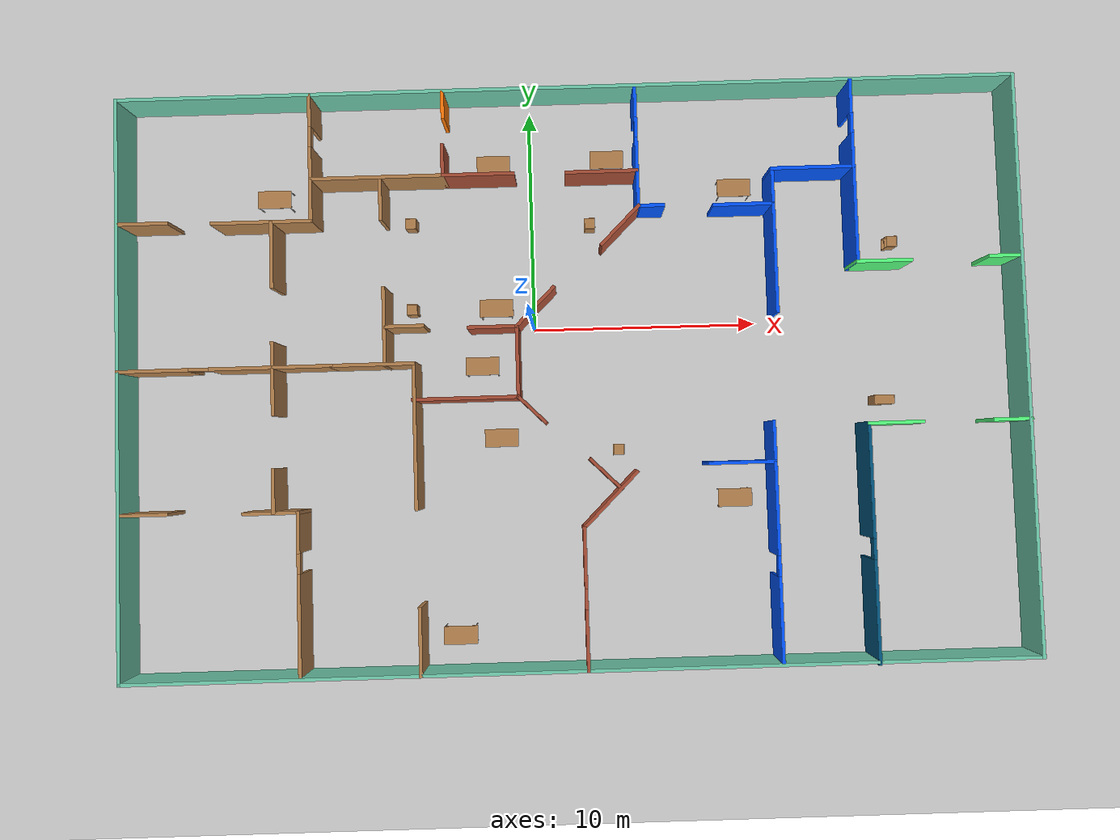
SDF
<sdf version="1.6">
 <world name="default">
  <light name="sun" type="directional">
   <pose>0 0 10 0 -0 0</pose>
   <diffuse>0.8 0.8 0.8 1</diffuse>
   <specular>0.2 0.2 0.2 1</specular>
   <attenuation>
    <range>1000</range>
    <constant>0.9</constant>
    <linear>0.01</linear>
    <quadratic>0.001</quadratic>
   </attenuation>
   <direction>-0.5 0.1 -0.9</direction>
  </light>
  <model name="ground_plane">
   <static>1</static>
   <link name="link">
    <collision name="collision">
     <geometry><plane><normal>0 0 1</normal><size>100 100</size></plane></geometry>
     <surface>
      <contact><collide_bitmask>65535</collide_bitmask></contact>
      <friction><ode><mu>100</mu><mu2>50</mu2></ode></friction>
     </surface>
    </collision>
    <visual name="visual">
     <cast_shadows>0</cast_shadows>
     <geometry><plane><normal>0 0 1</normal><size>100 100</size></plane></geometry>
     <material>
      <script><uri>file://media/materials/scripts/gazebo.material</uri><name>Gazebo/Grey</name></script>
     </material>
    </visual>
   </link>
  </model>
  <gravity>0 0 -9.8</gravity>
  <magnetic_field>6e-06 2.3e-05 -4.2e-05</magnetic_field>
  <atmosphere type="adiabatic"/>
  <physics name="default_physics" default="0" type="ode">
   <max_step_size>0.001</max_step_size>
   <real_time_factor>1</real_time_factor>
   <real_time_update_rate>1000</real_time_update_rate>
  </physics>
  <scene><ambient>0.4 0.4 0.4 1</ambient><background>0.7 0.7 0.7 1</background><shadows>1</shadows></scene>
  <spherical_coordinates>
   <surface_model>EARTH_WGS84</surface_model>
   <latitude_deg>0</latitude_deg>
   <longitude_deg>0</longitude_deg>
   <elevation>0</elevation>
   <heading_deg>0</heading_deg>
  </spherical_coordinates>
  <model name="Building">
   <pose>1.66654 -2.2526 0 0 -0 0</pose>
   <link name="Wall_1">
    <collision name="Wall_1_Collision">
     <geometry><box><size>40 0.15 2.5</size></box></geometry>
     <pose>0 0 1.25 0 -0 0</pose>
    </collision>
    <visual name="Wall_1_Visual">
     <pose>0 0 1.25 0 -0 0</pose>
     <geometry><box><size>40 0.15 2.5</size></box></geometry>
     <material>
      <script><uri>file://media/materials/scripts/gazebo.material</uri><name>Gazebo/Grey</name></script>
      <ambient>0.435294 0.796078 0.67451 1</ambient>
     </material>
     <meta><layer>0</layer></meta>
    </visual>
    <pose>-0.022022 12.8298 0 0 -0 0</pose>
   </link>
   <link name="Wall_15">
    <pose>-12.1346 -9.16282 0 0 -0 1.5708</pose>
    <visual name="Wall_15_Visual_0">
     <pose>-1.36925 0 1.25 0 -0 0</pose>
     <geometry><box><size>4.51149 0.15 2.5</size></box></geometry>
     <material>
      <script><uri>file://media/materials/scripts/gazebo.material</uri><name>Gazebo/Wood</name></script>
      <ambient>1 1 1 1</ambient>
     </material>
     <meta><layer>0</layer></meta>
    </visual>
    <collision name="Wall_15_Collision_0">
     <geometry><box><size>4.51149 0.15 2.5</size></box></geometry>
     <pose>-1.36925 0 1.25 0 -0 0</pose>
    </collision>
    <visual name="Wall_15_Visual_1">
     <pose>2.70575 0 1.25 0 -0 0</pose>
     <geometry><box><size>1.83851 0.15 2.5</size></box></geometry>
     <material>
      <script><uri>file://media/materials/scripts/gazebo.material</uri><name>Gazebo/Wood</name></script>
      <ambient>1 1 1 1</ambient>
     </material>
     <meta><layer>0</layer></meta>
    </visual>
    <collision name="Wall_15_Collision_1">
     <geometry><box><size>1.83851 0.15 2.5</size></box></geometry>
     <pose>2.70575 0 1.25 0 -0 0</pose>
    </collision>
    <visual name="Wall_15_Visual_2">
     <pose>1.33649 0 2.25 0 -0 0</pose>
     <geometry><box><size>0.9 0.15 0.5</size></box></geometry>
     <material>
      <script><uri>file://media/materials/scripts/gazebo.material</uri><name>Gazebo/Wood</name></script>
      <ambient>1 1 1 1</ambient>
     </material>
     <meta><layer>0</layer></meta>
    </visual>
    <collision name="Wall_15_Collision_2">
     <geometry><box><size>0.9 0.15 0.5</size></box></geometry>
     <pose>1.33649 0 2.25 0 -0 0</pose>
    </collision>
   </link>
   <link name="Wall_16">
    <collision name="Wall_16_Collision">
     <geometry><box><size>2.5 0.15 2.5</size></box></geometry>
     <pose>0 0 1.25 0 -0 0</pose>
    </collision>
    <visual name="Wall_16_Visual">
     <pose>0 0 1.25 0 -0 0</pose>
     <geometry><box><size>2.5 0.15 2.5</size></box></geometry>
     <material>
      <script><uri>file://media/materials/scripts/gazebo.material</uri><name>Gazebo/Wood</name></script>
      <ambient>1 1 1 1</ambient>
     </material>
     <meta><layer>0</layer></meta>
    </visual>
    <pose>-13.3096 -5.61282 0 0 -0 3.14159</pose>
   </link>
   <link name="Wall_18">
    <collision name="Wall_18_Collision">
     <geometry><box><size>2.25 0.15 2.5</size></box></geometry>
     <pose>0 0 1.25 0 -0 0</pose>
    </collision>
    <visual name="Wall_18_Visual">
     <pose>0 0 1.25 0 -0 0</pose>
     <geometry><box><size>2.25 0.15 2.5</size></box></geometry>
     <material>
      <script><uri>file://media/materials/scripts/gazebo.material</uri><name>Gazebo/Wood</name></script>
      <ambient>1 1 1 1</ambient>
     </material>
     <meta><layer>0</layer></meta>
    </visual>
    <pose>-18.8793 -5.52715 0 0 -0 0</pose>
   </link>
   <link name="Wall_2">
    <collision name="Wall_2_Collision">
     <geometry><box><size>25.75 0.15 2.5</size></box></geometry>
     <pose>0 0 1.25 0 -0 0</pose>
    </collision>
    <visual name="Wall_2_Visual">
     <pose>0 0 1.25 0 -0 0</pose>
     <geometry><box><size>25.75 0.15 2.5</size></box></geometry>
     <material>
      <script><uri>file://media/materials/scripts/gazebo.material</uri><name>Gazebo/Grey</name></script>
      <ambient>0.435294 0.796078 0.67451 1</ambient>
     </material>
     <meta><layer>0</layer></meta>
    </visual>
    <pose>19.903 0.029824 0 0 0 -1.5708</pose>
   </link>
   <link name="Wall_20">
    <collision name="Wall_20_Collision">
     <geometry><box><size>3 0.15 2.5</size></box></geometry>
     <pose>0 0 1.25 0 -0 0</pose>
    </collision>
    <visual name="Wall_20_Visual">
     <pose>0 0 1.25 0 -0 0</pose>
     <geometry><box><size>3 0.15 2.5</size></box></geometry>
     <material>
      <script><uri>file://media/materials/scripts/gazebo.material</uri><name>Gazebo/Wood</name></script>
      <ambient>1 1 1 1</ambient>
     </material>
     <meta><layer>0</layer></meta>
    </visual>
    <pose>-13.1276 5.72535 0 0 0 -1.5708</pose>
   </link>
   <link name="Wall_22">
    <collision name="Wall_22_Collision">
     <geometry><box><size>2 0.15 2.5</size></box></geometry>
     <pose>0 0 1.25 0 -0 0</pose>
    </collision>
    <visual name="Wall_22_Visual">
     <pose>0 0 1.25 0 -0 0</pose>
     <geometry><box><size>2 0.15 2.5</size></box></geometry>
     <material>
      <script><uri>file://media/materials/scripts/gazebo.material</uri><name>Gazebo/Wood</name></script>
      <ambient>1 1 1 1</ambient>
     </material>
     <meta><layer>0</layer></meta>
    </visual>
    <pose>-13.1876 -4.66182 0 0 -0 1.5708</pose>
   </link>
   <link name="Wall_24">
    <pose>-15.2543 0.737272 0 0 -0 0</pose>
    <visual name="Wall_24_Visual_0">
     <pose>-3.16583 0 1.25 0 -0 0</pose>
     <geometry><box><size>3.16833 0.15 2.5</size></box></geometry>
     <material>
      <script><uri>file://media/materials/scripts/gazebo.material</uri><name>Gazebo/Wood</name></script>
      <ambient>1 1 1 1</ambient>
     </material>
     <meta><layer>0</layer></meta>
    </visual>
    <collision name="Wall_24_Collision_0">
     <geometry><box><size>3.16833 0.15 2.5</size></box></geometry>
     <pose>-3.16583 0 1.25 0 -0 0</pose>
    </collision>
    <visual name="Wall_24_Visual_1">
     <pose>2.03417 0 1.25 0 -0 0</pose>
     <geometry><box><size>5.43166 0.15 2.5</size></box></geometry>
     <material>
      <script><uri>file://media/materials/scripts/gazebo.material</uri><name>Gazebo/Wood</name></script>
      <ambient>1 1 1 1</ambient>
     </material>
     <meta><layer>0</layer></meta>
    </visual>
    <collision name="Wall_24_Collision_1">
     <geometry><box><size>5.43166 0.15 2.5</size></box></geometry>
     <pose>2.03417 0 1.25 0 -0 0</pose>
    </collision>
    <visual name="Wall_24_Visual_2">
     <pose>-1.13166 0 2.25 0 -0 0</pose>
     <geometry><box><size>0.9 0.15 0.5</size></box></geometry>
     <material>
      <script><uri>file://media/materials/scripts/gazebo.material</uri><name>Gazebo/Wood</name></script>
      <ambient>1 1 1 1</ambient>
     </material>
     <meta><layer>0</layer></meta>
    </visual>
    <collision name="Wall_24_Collision_2">
     <geometry><box><size>0.9 0.15 0.5</size></box></geometry>
     <pose>-1.13166 0 2.25 0 -0 0</pose>
    </collision>
   </link>
   <link name="Wall_26">
    <collision name="Wall_26_Collision">
     <geometry><box><size>3.25 0.15 2.5</size></box></geometry>
     <pose>0 0 1.25 0 -0 0</pose>
    </collision>
    <visual name="Wall_26_Visual">
     <pose>0 0 1.25 0 -0 0</pose>
     <geometry><box><size>3.25 0.15 2.5</size></box></geometry>
     <material>
      <script><uri>file://media/materials/scripts/gazebo.material</uri><name>Gazebo/Wood</name></script>
      <ambient>1 1 1 1</ambient>
     </material>
     <meta><layer>0</layer></meta>
    </visual>
    <pose>-13.1573 0.242073 0 0 0 -1.5708</pose>
   </link>
   <link name="Wall_29">
    <pose>12.8432 -7.65482 0 0 -0 1.5708</pose>
    <visual name="Wall_29_Visual_0">
     <pose>-2.98763 0 1.25 0 -0 0</pose>
     <geometry><box><size>4.52474 0.15 2.5</size></box></geometry>
     <material>
      <script><uri>file://media/materials/scripts/gazebo.material</uri><name>Gazebo/Grey</name></script>
      <ambient>0 0.333333 0.498039 1</ambient>
     </material>
     <meta><layer>0</layer></meta>
    </visual>
    <collision name="Wall_29_Collision_0">
     <geometry><box><size>4.52474 0.15 2.5</size></box></geometry>
     <pose>-2.98763 0 1.25 0 -0 0</pose>
    </collision>
    <visual name="Wall_29_Visual_1">
     <pose>2.71237 0 1.25 0 -0 0</pose>
     <geometry><box><size>5.07526 0.15 2.5</size></box></geometry>
     <material>
      <script><uri>file://media/materials/scripts/gazebo.material</uri><name>Gazebo/Grey</name></script>
      <ambient>0 0.333333 0.498039 1</ambient>
     </material>
     <meta><layer>0</layer></meta>
    </visual>
    <collision name="Wall_29_Collision_1">
     <geometry><box><size>5.07526 0.15 2.5</size></box></geometry>
     <pose>2.71237 0 1.25 0 -0 0</pose>
    </collision>
    <visual name="Wall_29_Visual_2">
     <pose>-0.275263 0 2.25 0 -0 0</pose>
     <geometry><box><size>0.9 0.15 0.5</size></box></geometry>
     <material>
      <script><uri>file://media/materials/scripts/gazebo.material</uri><name>Gazebo/Grey</name></script>
      <ambient>0 0.333333 0.498039 1</ambient>
     </material>
     <meta><layer>0</layer></meta>
    </visual>
    <collision name="Wall_29_Collision_2">
     <geometry><box><size>0.9 0.15 0.5</size></box></geometry>
     <pose>-0.275263 0 2.25 0 -0 0</pose>
    </collision>
   </link>
   <link name="Wall_3">
    <collision name="Wall_3_Collision">
     <geometry><box><size>40 0.15 2.5</size></box></geometry>
     <pose>0 0 1.25 0 -0 0</pose>
    </collision>
    <visual name="Wall_3_Visual">
     <pose>0 0 1.25 0 -0 0</pose>
     <geometry><box><size>40 0.15 2.5</size></box></geometry>
     <material>
      <script><uri>file://media/materials/scripts/gazebo.material</uri><name>Gazebo/Grey</name></script>
      <ambient>0.435294 0.796078 0.67451 1</ambient>
     </material>
     <meta><layer>0</layer></meta>
    </visual>
    <pose>-0.022022 -12.7702 0 0 -0 3.14159</pose>
   </link>
   <link name="Wall_30">
    <collision name="Wall_30_Collision">
     <geometry><box><size>2.5 0.15 2.5</size></box></geometry>
     <pose>0 0 1.25 0 -0 0</pose>
    </collision>
    <visual name="Wall_30_Visual">
     <pose>0 0 1.25 0 -0 0</pose>
     <geometry><box><size>2.5 0.15 2.5</size></box></geometry>
     <material>
      <script><uri>file://media/materials/scripts/gazebo.material</uri><name>Gazebo/Grey</name></script>
      <ambient>0.333333 1 0.498039 1</ambient>
     </material>
     <meta><layer>0</layer></meta>
    </visual>
    <pose>14.0182 -2.47982 0 0 -0 0</pose>
   </link>
   <link name="Wall_32">
    <collision name="Wall_32_Collision">
     <geometry><box><size>1.75 0.15 2.5</size></box></geometry>
     <pose>0 0 1.25 0 -0 0</pose>
    </collision>
    <visual name="Wall_32_Visual">
     <pose>0 0 1.25 0 -0 0</pose>
     <geometry><box><size>1.75 0.15 2.5</size></box></geometry>
     <material>
      <script><uri>file://media/materials/scripts/gazebo.material</uri><name>Gazebo/Grey</name></script>
      <ambient>0.333333 1 0.498039 1</ambient>
     </material>
     <meta><layer>0</layer></meta>
    </visual>
    <pose>19.147 -2.48795 0 0 -0 3.14159</pose>
   </link>
   <link name="Wall_34">
    <collision name="Wall_34_Collision">
     <geometry><box><size>1.5 0.15 2.5</size></box></geometry>
     <pose>0 0 1.25 0 -0 0</pose>
    </collision>
    <visual name="Wall_34_Visual">
     <pose>0 0 1.25 0 -0 0</pose>
     <geometry><box><size>1.5 0.15 2.5</size></box></geometry>
     <material>
      <script><uri>file://media/materials/scripts/gazebo.material</uri><name>Gazebo/Grey</name></script>
      <ambient>0.333333 1 0.498039 1</ambient>
     </material>
     <meta><layer>0</layer></meta>
    </visual>
    <pose>19.2034 4.71614 0 0 -0 3.14159</pose>
   </link>
   <link name="Wall_36">
    <pose>12.6743 8.69753 0 0 -0 1.5708</pose>
    <visual name="Wall_36_Visual_0">
     <pose>-1.21115 0 1.25 0 -0 0</pose>
     <geometry><box><size>5.8277 0.15 2.5</size></box></geometry>
     <material>
      <script><uri>file://media/materials/scripts/gazebo.material</uri><name>Gazebo/Grey</name></script>
      <ambient>0 0.333333 1 1</ambient>
     </material>
     <meta><layer>0</layer></meta>
    </visual>
    <collision name="Wall_36_Collision_0">
     <geometry><box><size>5.8277 0.15 2.5</size></box></geometry>
     <pose>-1.21115 0 1.25 0 -0 0</pose>
    </collision>
    <visual name="Wall_36_Visual_1">
     <pose>3.36385 0 1.25 0 -0 0</pose>
     <geometry><box><size>1.52231 0.15 2.5</size></box></geometry>
     <material>
      <script><uri>file://media/materials/scripts/gazebo.material</uri><name>Gazebo/Grey</name></script>
      <ambient>0 0.333333 1 1</ambient>
     </material>
     <meta><layer>0</layer></meta>
    </visual>
    <collision name="Wall_36_Collision_1">
     <geometry><box><size>1.52231 0.15 2.5</size></box></geometry>
     <pose>3.36385 0 1.25 0 -0 0</pose>
    </collision>
    <visual name="Wall_36_Visual_2">
     <pose>2.1527 0 2.25 0 -0 0</pose>
     <geometry><box><size>0.9 0.15 0.5</size></box></geometry>
     <material>
      <script><uri>file://media/materials/scripts/gazebo.material</uri><name>Gazebo/Grey</name></script>
      <ambient>0 0.333333 1 1</ambient>
     </material>
     <meta><layer>0</layer></meta>
    </visual>
    <collision name="Wall_36_Collision_2">
     <geometry><box><size>0.9 0.15 0.5</size></box></geometry>
     <pose>2.1527 0 2.25 0 -0 0</pose>
    </collision>
   </link>
   <link name="Wall_38">
    <collision name="Wall_38_Collision">
     <geometry><box><size>2.5 0.15 2.5</size></box></geometry>
     <pose>0 0 1.25 0 -0 0</pose>
    </collision>
    <visual name="Wall_38_Visual">
     <pose>0 0 1.25 0 -0 0</pose>
     <geometry><box><size>2.5 0.15 2.5</size></box></geometry>
     <material>
      <script><uri>file://media/materials/scripts/gazebo.material</uri><name>Gazebo/Grey</name></script>
      <ambient>0.333333 1 0.498039 1</ambient>
     </material>
     <meta><layer>0</layer></meta>
    </visual>
    <pose>13.8493 4.64753 0 0 -0 0</pose>
   </link>
   <link name="Wall_4">
    <collision name="Wall_4_Collision">
     <geometry><box><size>25.75 0.15 2.5</size></box></geometry>
     <pose>0 0 1.25 0 -0 0</pose>
    </collision>
    <visual name="Wall_4_Visual">
     <pose>0 0 1.25 0 -0 0</pose>
     <geometry><box><size>25.75 0.15 2.5</size></box></geometry>
     <material>
      <script><uri>file://media/materials/scripts/gazebo.material</uri><name>Gazebo/Grey</name></script>
      <ambient>0.435294 0.796078 0.67451 1</ambient>
     </material>
     <meta><layer>0</layer></meta>
    </visual>
    <pose>-19.947 0.029824 0 0 -0 1.5708</pose>
   </link>
   <link name="Wall_40">
    <collision name="Wall_40_Collision">
     <geometry><box><size>3.75 0.15 2.5</size></box></geometry>
     <pose>0 0 1.25 0 -0 0</pose>
    </collision>
    <visual name="Wall_40_Visual">
     <pose>0 0 1.25 0 -0 0</pose>
     <geometry><box><size>3.75 0.15 2.5</size></box></geometry>
     <material>
      <script><uri>file://media/materials/scripts/gazebo.material</uri><name>Gazebo/Grey</name></script>
      <ambient>0 0.333333 1 1</ambient>
     </material>
     <meta><layer>0</layer></meta>
    </visual>
    <pose>10.8525 8.90126 0 0 -0 3.14159</pose>
   </link>
   <link name="Wall_41">
    <collision name="Wall_41_Collision">
     <geometry><box><size>6.5 0.15 2.5</size></box></geometry>
     <pose>0 0 1.25 0 -0 0</pose>
    </collision>
    <visual name="Wall_41_Visual">
     <pose>0 0 1.25 0 -0 0</pose>
     <geometry><box><size>6.5 0.15 2.5</size></box></geometry>
     <material>
      <script><uri>file://media/materials/scripts/gazebo.material</uri><name>Gazebo/Grey</name></script>
      <ambient>0 0.333333 1 1</ambient>
     </material>
     <meta><layer>0</layer></meta>
    </visual>
    <pose>9.05253 5.72626 0 0 0 -1.5708</pose>
   </link>
   <link name="Wall_46">
    <pose>8.69095 -7.47844 0 0 -0 1.5708</pose>
    <visual name="Wall_46_Visual_0">
     <pose>-3.3871 0 1.25 0 -0 0</pose>
     <geometry><box><size>3.7258 0.15 2.5</size></box></geometry>
     <material>
      <script><uri>file://media/materials/scripts/gazebo.material</uri><name>Gazebo/Grey</name></script>
      <ambient>0 0.333333 1 1</ambient>
     </material>
     <meta><layer>0</layer></meta>
    </visual>
    <collision name="Wall_46_Collision_0">
     <geometry><box><size>3.7258 0.15 2.5</size></box></geometry>
     <pose>-3.3871 0 1.25 0 -0 0</pose>
    </collision>
    <visual name="Wall_46_Visual_1">
     <pose>2.3129 0 1.25 0 -0 0</pose>
     <geometry><box><size>5.8742 0.15 2.5</size></box></geometry>
     <material>
      <script><uri>file://media/materials/scripts/gazebo.material</uri><name>Gazebo/Grey</name></script>
      <ambient>0 0.333333 1 1</ambient>
     </material>
     <meta><layer>0</layer></meta>
    </visual>
    <collision name="Wall_46_Collision_1">
     <geometry><box><size>5.8742 0.15 2.5</size></box></geometry>
     <pose>2.3129 0 1.25 0 -0 0</pose>
    </collision>
    <visual name="Wall_46_Visual_2">
     <pose>-1.0742 0 2.25 0 -0 0</pose>
     <geometry><box><size>0.9 0.15 0.5</size></box></geometry>
     <material>
      <script><uri>file://media/materials/scripts/gazebo.material</uri><name>Gazebo/Grey</name></script>
      <ambient>0 0.333333 1 1</ambient>
     </material>
     <meta><layer>0</layer></meta>
    </visual>
    <collision name="Wall_46_Collision_2">
     <geometry><box><size>0.9 0.15 0.5</size></box></geometry>
     <pose>-1.0742 0 2.25 0 -0 0</pose>
    </collision>
   </link>
   <link name="Wall_48">
    <collision name="Wall_48_Collision">
     <geometry><box><size>6 0.15 2.5</size></box></geometry>
     <pose>0 0 1.25 0 -0 0</pose>
    </collision>
    <visual name="Wall_48_Visual">
     <pose>0 0 1.25 0 -0 0</pose>
     <geometry><box><size>6 0.15 2.5</size></box></geometry>
     <material>
      <script><uri>file://media/materials/scripts/gazebo.material</uri><name>Gazebo/Wood</name></script>
      <ambient>1 1 1 1</ambient>
     </material>
     <meta><layer>0</layer></meta>
    </visual>
    <pose>-8.43698 9.03275 0 0 -0 0</pose>
   </link>
   <link name="Wall_54">
    <collision name="Wall_54_Collision">
     <geometry><box><size>3.75 0.15 2.5</size></box></geometry>
     <pose>0 0 1.25 0 -0 0</pose>
    </collision>
    <visual name="Wall_54_Visual">
     <pose>0 0 1.25 0 -0 0</pose>
     <geometry><box><size>3.75 0.15 2.5</size></box></geometry>
     <material>
      <script><uri>file://media/materials/scripts/gazebo.material</uri><name>Gazebo/Wood</name></script>
      <ambient>1 1 1 1</ambient>
     </material>
     <meta><layer>0</layer></meta>
    </visual>
    <pose>-8.77934 0.737272 0 0 -0 0</pose>
   </link>
   <link name="Wall_55">
    <collision name="Wall_55_Collision">
     <geometry><box><size>6.5 0.15 2.5</size></box></geometry>
     <pose>0 0 1.25 0 -0 0</pose>
    </collision>
    <visual name="Wall_55_Visual">
     <pose>0 0 1.25 0 -0 0</pose>
     <geometry><box><size>6.5 0.15 2.5</size></box></geometry>
     <material>
      <script><uri>file://media/materials/scripts/gazebo.material</uri><name>Gazebo/Wood</name></script>
      <ambient>1 1 1 1</ambient>
     </material>
     <meta><layer>0</layer></meta>
    </visual>
    <pose>-6.97934 -2.43773 0 0 0 -1.5708</pose>
   </link>
   <link name="Wall_57">
    <collision name="Wall_57_Collision">
     <geometry><box><size>3 0.15 2.5</size></box></geometry>
     <pose>0 0 1.25 0 -0 0</pose>
    </collision>
    <visual name="Wall_57_Visual">
     <pose>0 0 1.25 0 -0 0</pose>
     <geometry><box><size>3 0.15 2.5</size></box></geometry>
     <material>
      <script><uri>file://media/materials/scripts/gazebo.material</uri><name>Gazebo/Wood</name></script>
      <ambient>1 1 1 1</ambient>
     </material>
     <meta><layer>0</layer></meta>
    </visual>
    <pose>-6.93144 -11.3458 0 0 -0 1.5708</pose>
   </link>
   <link name="Wall_59">
    <collision name="Wall_59_Collision">
     <geometry><box><size>4.75 0.15 2.5</size></box></geometry>
     <pose>0 0 1.25 0 -0 0</pose>
    </collision>
    <visual name="Wall_59_Visual">
     <pose>0 0 1.25 0 -0 0</pose>
     <geometry><box><size>4.75 0.15 2.5</size></box></geometry>
     <material>
      <script><uri>file://media/materials/scripts/gazebo.material</uri><name>Gazebo/Bricks</name></script>
      <ambient>1 1 1 1</ambient>
     </material>
     <meta><layer>0</layer></meta>
    </visual>
    <pose>-4.72167 -0.861079 0 0 -0 0</pose>
   </link>
   <link name="Wall_6">
    <collision name="Wall_6_Collision">
     <geometry><box><size>2.25 0.15 2.5</size></box></geometry>
     <pose>0 0 1.25 0 -0 0</pose>
    </collision>
    <visual name="Wall_6_Visual">
     <pose>0 0 1.25 0 -0 0</pose>
     <geometry><box><size>2.25 0.15 2.5</size></box></geometry>
     <material>
      <script><uri>file://media/materials/scripts/gazebo.material</uri><name>Gazebo/Wood</name></script>
      <ambient>1 1 1 1</ambient>
     </material>
     <meta><layer>0</layer></meta>
    </visual>
    <pose>-18.7981 7.25334 0 0 -0 0</pose>
   </link>
   <link name="Wall_61">
    <pose>0.286548 -9.72076 0 0 -0 1.5708</pose>
    <visual name="Wall_61_Visual_0">
     <pose>-1.77411 0 1.25 0 -0 0</pose>
     <geometry><box><size>2.70178 0.15 2.5</size></box></geometry>
     <material>
      <script><uri>file://media/materials/scripts/gazebo.material</uri><name>Gazebo/Bricks</name></script>
      <ambient>1 1 1 1</ambient>
     </material>
     <meta><layer>0</layer></meta>
    </visual>
    <collision name="Wall_61_Collision_0">
     <geometry><box><size>2.70178 0.15 2.5</size></box></geometry>
     <pose>-1.77411 0 1.25 0 -0 0</pose>
    </collision>
    <visual name="Wall_61_Visual_1">
     <pose>1.80089 0 1.25 0 -0 0</pose>
     <geometry><box><size>2.64822 0.15 2.5</size></box></geometry>
     <material>
      <script><uri>file://media/materials/scripts/gazebo.material</uri><name>Gazebo/Bricks</name></script>
      <ambient>1 1 1 1</ambient>
     </material>
     <meta><layer>0</layer></meta>
    </visual>
    <collision name="Wall_61_Collision_1">
     <geometry><box><size>2.64822 0.15 2.5</size></box></geometry>
     <pose>1.80089 0 1.25 0 -0 0</pose>
    </collision>
    <visual name="Wall_61_Visual_2">
     <pose>0.026779 0 2.25 0 -0 0</pose>
     <geometry><box><size>0.9 0.15 0.5</size></box></geometry>
     <material>
      <script><uri>file://media/materials/scripts/gazebo.material</uri><name>Gazebo/Bricks</name></script>
      <ambient>1 1 1 1</ambient>
     </material>
     <meta><layer>0</layer></meta>
    </visual>
    <collision name="Wall_61_Collision_2">
     <geometry><box><size>0.9 0.15 0.5</size></box></geometry>
     <pose>0.026779 0 2.25 0 -0 0</pose>
    </collision>
   </link>
   <link name="Wall_63">
    <collision name="Wall_63_Collision">
     <geometry><box><size>3 0.15 2.5</size></box></geometry>
     <pose>0 0 1.25 0 -0 0</pose>
    </collision>
    <visual name="Wall_63_Visual">
     <pose>0 0 1.25 0 -0 0</pose>
     <geometry><box><size>3 0.15 2.5</size></box></geometry>
     <material>
      <script><uri>file://media/materials/scripts/gazebo.material</uri><name>Gazebo/Grey</name></script>
      <ambient>0 0.333333 1 1</ambient>
     </material>
     <meta><layer>0</layer></meta>
    </visual>
    <pose>7.25246 -4.01895 0 0 -0 3.14159</pose>
   </link>
   <link name="Wall_66">
    <collision name="Wall_66_Collision">
     <geometry><box><size>3.5 0.15 2.5</size></box></geometry>
     <pose>0 0 1.25 0 -0 0</pose>
    </collision>
    <visual name="Wall_66_Visual">
     <pose>0 0 1.25 0 -0 0</pose>
     <geometry><box><size>3.5 0.15 2.5</size></box></geometry>
     <material>
      <script><uri>file://media/materials/scripts/gazebo.material</uri><name>Gazebo/Bricks</name></script>
      <ambient>1 1 1 1</ambient>
     </material>
     <meta><layer>0</layer></meta>
    </visual>
    <pose>1.47095 -5.48636 0 0 -0 0.785398</pose>
   </link>
   <link name="Wall_68">
    <collision name="Wall_68_Collision">
     <geometry><box><size>1.75 0.15 2.5</size></box></geometry>
     <pose>0 0 1.25 0 -0 0</pose>
    </collision>
    <visual name="Wall_68_Visual">
     <pose>0 0 1.25 0 -0 0</pose>
     <geometry><box><size>1.75 0.15 2.5</size></box></geometry>
     <material>
      <script><uri>file://media/materials/scripts/gazebo.material</uri><name>Gazebo/Bricks</name></script>
      <ambient>1 1 1 1</ambient>
     </material>
     <meta><layer>0</layer></meta>
    </visual>
    <pose>-1.85598 -1.42676 0 0 0 -0.785398</pose>
   </link>
   <link name="Wall_70">
    <collision name="Wall_70_Collision">
     <geometry><box><size>2 0.15 2.5</size></box></geometry>
     <pose>0 0 1.25 0 -0 0</pose>
    </collision>
    <visual name="Wall_70_Visual">
     <pose>0 0 1.25 0 -0 0</pose>
     <geometry><box><size>2 0.15 2.5</size></box></geometry>
     <material>
      <script><uri>file://media/materials/scripts/gazebo.material</uri><name>Gazebo/Bricks</name></script>
      <ambient>1 1 1 1</ambient>
     </material>
     <meta><layer>0</layer></meta>
    </visual>
    <pose>1.31835 -4.36146 0 0 -0 2.35619</pose>
   </link>
   <link name="Wall_72">
    <collision name="Wall_72_Collision">
     <geometry><box><size>3.5 0.15 2.5</size></box></geometry>
     <pose>0 0 1.25 0 -0 0</pose>
    </collision>
    <visual name="Wall_72_Visual">
     <pose>0 0 1.25 0 -0 0</pose>
     <geometry><box><size>3.5 0.15 2.5</size></box></geometry>
     <material>
      <script><uri>file://media/materials/scripts/gazebo.material</uri><name>Gazebo/Wood</name></script>
      <ambient>1 1 1 1</ambient>
     </material>
     <meta><layer>0</layer></meta>
    </visual>
    <pose>-8.23539 2.39683 0 0 -0 1.5708</pose>
   </link>
   <link name="Wall_74">
    <collision name="Wall_74_Collision">
     <geometry><box><size>2 0.15 2.5</size></box></geometry>
     <pose>0 0 1.25 0 -0 0</pose>
    </collision>
    <visual name="Wall_74_Visual">
     <pose>0 0 1.25 0 -0 0</pose>
     <geometry><box><size>2 0.15 2.5</size></box></geometry>
     <material>
      <script><uri>file://media/materials/scripts/gazebo.material</uri><name>Gazebo/Wood</name></script>
      <ambient>1 1 1 1</ambient>
     </material>
     <meta><layer>0</layer></meta>
    </visual>
    <pose>-8.29471 8.10224 0 0 0 -1.5708</pose>
   </link>
   <link name="Wall_76">
    <collision name="Wall_76_Collision">
     <geometry><box><size>3.25 0.15 2.5</size></box></geometry>
     <pose>0 0 1.25 0 -0 0</pose>
    </collision>
    <visual name="Wall_76_Visual">
     <pose>0 0 1.25 0 -0 0</pose>
     <geometry><box><size>3.25 0.15 2.5</size></box></geometry>
     <material>
      <script><uri>file://media/materials/scripts/gazebo.material</uri><name>Gazebo/Bricks</name></script>
      <ambient>1 1 1 1</ambient>
     </material>
     <meta><layer>0</layer></meta>
    </visual>
    <pose>-2.42167 0.688921 0 0 -0 1.5708</pose>
   </link>
   <link name="Wall_77">
    <collision name="Wall_77_Collision">
     <geometry><box><size>2.25 0.15 2.5</size></box></geometry>
     <pose>0 0 1.25 0 -0 0</pose>
    </collision>
    <visual name="Wall_77_Visual">
     <pose>0 0 1.25 0 -0 0</pose>
     <geometry><box><size>2.25 0.15 2.5</size></box></geometry>
     <material>
      <script><uri>file://media/materials/scripts/gazebo.material</uri><name>Gazebo/Bricks</name></script>
      <ambient>1 1 1 1</ambient>
     </material>
     <meta><layer>0</layer></meta>
    </visual>
    <pose>-3.47167 2.23892 0 0 -0 3.14159</pose>
   </link>
   <link name="Wall_79">
    <collision name="Wall_79_Collision">
     <geometry><box><size>1.75 0.15 2.5</size></box></geometry>
     <pose>0 0 1.25 0 -0 0</pose>
    </collision>
    <visual name="Wall_79_Visual">
     <pose>0 0 1.25 0 -0 0</pose>
     <geometry><box><size>1.75 0.15 2.5</size></box></geometry>
     <material>
      <script><uri>file://media/materials/scripts/gazebo.material</uri><name>Gazebo/Wood</name></script>
      <ambient>1 1 1 1</ambient>
     </material>
     <meta><layer>0</layer></meta>
    </visual>
    <pose>-7.36493 2.38138 0 0 -0 0</pose>
   </link>
   <link name="Wall_8">
    <collision name="Wall_8_Collision">
     <geometry><box><size>4.5 0.15 2.5</size></box></geometry>
     <pose>0 0 1.25 0 -0 0</pose>
    </collision>
    <visual name="Wall_8_Visual">
     <pose>0 0 1.25 0 -0 0</pose>
     <geometry><box><size>4.5 0.15 2.5</size></box></geometry>
     <material>
      <script><uri>file://media/materials/scripts/gazebo.material</uri><name>Gazebo/Wood</name></script>
      <ambient>1 1 1 1</ambient>
     </material>
     <meta><layer>0</layer></meta>
    </visual>
    <pose>-13.5469 7.17399 0 0 -0 0</pose>
   </link>
   <link name="Wall_81">
    <collision name="Wall_81_Collision">
     <geometry><box><size>1.5 0.15 2.5</size></box></geometry>
     <pose>0 0 1.25 0 -0 0</pose>
    </collision>
    <visual name="Wall_81_Visual">
     <pose>0 0 1.25 0 -0 0</pose>
     <geometry><box><size>1.5 0.15 2.5</size></box></geometry>
     <material>
      <script><uri>file://media/materials/scripts/gazebo.material</uri><name>Gazebo/Bricks</name></script>
      <ambient>1 1 1 1</ambient>
     </material>
     <meta><layer>0</layer></meta>
    </visual>
    <pose>-5.51198 9.70776 0 0 -0 1.5708</pose>
   </link>
   <link name="Wall_85">
    <collision name="Wall_85_Collision">
     <geometry><box><size>1.25 0.15 2.5</size></box></geometry>
     <pose>0 0 1.25 0 -0 0</pose>
    </collision>
    <visual name="Wall_85_Visual">
     <pose>0 0 1.25 0 -0 0</pose>
     <geometry><box><size>1.25 0.15 2.5</size></box></geometry>
     <material>
      <script><uri>file://media/materials/scripts/gazebo.material</uri><name>Gazebo/Grey</name></script>
      <ambient>0.996078 0.47451 0.0196078 1</ambient>
     </material>
     <meta><layer>0</layer></meta>
    </visual>
    <pose>-5.45501 12.2092 0 0 0 -1.5708</pose>
   </link>
   <link name="Wall_87">
    <collision name="Wall_87_Collision">
     <geometry><box><size>2.75 0.15 2.5</size></box></geometry>
     <pose>0 0 1.25 0 -0 0</pose>
    </collision>
    <visual name="Wall_87_Visual">
     <pose>0 0 1.25 0 -0 0</pose>
     <geometry><box><size>2.75 0.15 2.5</size></box></geometry>
     <material>
      <script><uri>file://media/materials/scripts/gazebo.material</uri><name>Gazebo/Grey</name></script>
      <ambient>0 0.333333 1 1</ambient>
     </material>
     <meta><layer>0</layer></meta>
    </visual>
    <pose>7.75943 7.34571 0 0 -0 3.14159</pose>
   </link>
   <link name="Wall_89">
    <pose>3.09674 10.0842 0 0 0 -1.5708</pose>
    <visual name="Wall_89_Visual_0">
     <pose>-2.03489 0 1.25 0 -0 0</pose>
     <geometry><box><size>1.43023 0.15 2.5</size></box></geometry>
     <material>
      <script><uri>file://media/materials/scripts/gazebo.material</uri><name>Gazebo/Grey</name></script>
      <ambient>0 0.333333 1 1</ambient>
     </material>
     <meta><layer>0</layer></meta>
    </visual>
    <collision name="Wall_89_Collision_0">
     <geometry><box><size>1.43023 0.15 2.5</size></box></geometry>
     <pose>-2.03489 0 1.25 0 -0 0</pose>
    </collision>
    <visual name="Wall_89_Visual_1">
     <pose>1.16511 0 1.25 0 -0 0</pose>
     <geometry><box><size>3.16977 0.15 2.5</size></box></geometry>
     <material>
      <script><uri>file://media/materials/scripts/gazebo.material</uri><name>Gazebo/Grey</name></script>
      <ambient>0 0.333333 1 1</ambient>
     </material>
     <meta><layer>0</layer></meta>
    </visual>
    <collision name="Wall_89_Collision_1">
     <geometry><box><size>3.16977 0.15 2.5</size></box></geometry>
     <pose>1.16511 0 1.25 0 -0 0</pose>
    </collision>
    <visual name="Wall_89_Visual_2">
     <pose>-0.869774 0 2.25 0 -0 0</pose>
     <geometry><box><size>0.9 0.15 0.5</size></box></geometry>
     <material>
      <script><uri>file://media/materials/scripts/gazebo.material</uri><name>Gazebo/Grey</name></script>
      <ambient>0 0.333333 1 1</ambient>
     </material>
     <meta><layer>0</layer></meta>
    </visual>
    <collision name="Wall_89_Collision_2">
     <geometry><box><size>0.9 0.15 0.5</size></box></geometry>
     <pose>-0.869774 0 2.25 0 -0 0</pose>
    </collision>
   </link>
   <link name="Wall_9">
    <pose>-11.3719 9.97399 0 0 -0 1.5708</pose>
    <visual name="Wall_9_Visual_0">
     <pose>-1.1725 0 1.25 0 -0 0</pose>
     <geometry><box><size>3.40499 0.15 2.5</size></box></geometry>
     <material>
      <script><uri>file://media/materials/scripts/gazebo.material</uri><name>Gazebo/Wood</name></script>
      <ambient>1 1 1 1</ambient>
     </material>
     <meta><layer>0</layer></meta>
    </visual>
    <collision name="Wall_9_Collision_0">
     <geometry><box><size>3.40499 0.15 2.5</size></box></geometry>
     <pose>-1.1725 0 1.25 0 -0 0</pose>
    </collision>
    <visual name="Wall_9_Visual_1">
     <pose>2.1525 0 1.25 0 -0 0</pose>
     <geometry><box><size>1.44501 0.15 2.5</size></box></geometry>
     <material>
      <script><uri>file://media/materials/scripts/gazebo.material</uri><name>Gazebo/Wood</name></script>
      <ambient>1 1 1 1</ambient>
     </material>
     <meta><layer>0</layer></meta>
    </visual>
    <collision name="Wall_9_Collision_1">
     <geometry><box><size>1.44501 0.15 2.5</size></box></geometry>
     <pose>2.1525 0 1.25 0 -0 0</pose>
    </collision>
    <visual name="Wall_9_Visual_2">
     <pose>0.979991 0 2.25 0 -0 0</pose>
     <geometry><box><size>0.9 0.15 0.5</size></box></geometry>
     <material>
      <script><uri>file://media/materials/scripts/gazebo.material</uri><name>Gazebo/Wood</name></script>
      <ambient>1 1 1 1</ambient>
     </material>
     <meta><layer>0</layer></meta>
    </visual>
    <collision name="Wall_9_Collision_2">
     <geometry><box><size>0.9 0.15 0.5</size></box></geometry>
     <pose>0.979991 0 2.25 0 -0 0</pose>
    </collision>
   </link>
   <link name="Wall_90">
    <collision name="Wall_90_Collision">
     <geometry><box><size>1.25 0.15 2.5</size></box></geometry>
     <pose>0 0 1.25 0 -0 0</pose>
    </collision>
    <visual name="Wall_90_Visual">
     <pose>0 0 1.25 0 -0 0</pose>
     <geometry><box><size>1.25 0.15 2.5</size></box></geometry>
     <material>
      <script><uri>file://media/materials/scripts/gazebo.material</uri><name>Gazebo/Grey</name></script>
      <ambient>0 0.333333 1 1</ambient>
     </material>
     <meta><layer>0</layer></meta>
    </visual>
    <pose>3.64674 7.40921 0 0 -0 0</pose>
   </link>
   <link name="Wall_92">
    <collision name="Wall_92_Collision">
     <geometry><box><size>3.25 0.15 2.5</size></box></geometry>
     <pose>0 0 1.25 0 -0 0</pose>
    </collision>
    <visual name="Wall_92_Visual">
     <pose>0 0 1.25 0 -0 0</pose>
     <geometry><box><size>3.25 0.15 2.5</size></box></geometry>
     <material>
      <script><uri>file://media/materials/scripts/gazebo.material</uri><name>Gazebo/Bricks</name></script>
      <ambient>1 1 1 1</ambient>
     </material>
     <meta><layer>0</layer></meta>
    </visual>
    <pose>-3.96198 9.03275 0 0 -0 0</pose>
   </link>
   <link name="Wall_94">
    <collision name="Wall_94_Collision">
     <geometry><box><size>3.25 0.15 2.5</size></box></geometry>
     <pose>0 0 1.25 0 -0 0</pose>
    </collision>
    <visual name="Wall_94_Visual">
     <pose>0 0 1.25 0 -0 0</pose>
     <geometry><box><size>3.25 0.15 2.5</size></box></geometry>
     <material>
      <script><uri>file://media/materials/scripts/gazebo.material</uri><name>Gazebo/Bricks</name></script>
      <ambient>1 1 1 1</ambient>
     </material>
     <meta><layer>0</layer></meta>
    </visual>
    <pose>1.50848 8.9933 0 0 -0 0</pose>
   </link>
   <link name="Wall_96">
    <collision name="Wall_96_Collision">
     <geometry><box><size>2.5 0.15 2.5</size></box></geometry>
     <pose>0 0 1.25 0 -0 0</pose>
    </collision>
    <visual name="Wall_96_Visual">
     <pose>0 0 1.25 0 -0 0</pose>
     <geometry><box><size>2.5 0.15 2.5</size></box></geometry>
     <material>
      <script><uri>file://media/materials/scripts/gazebo.material</uri><name>Gazebo/Bricks</name></script>
      <ambient>1 1 1 1</ambient>
     </material>
     <meta><layer>0</layer></meta>
    </visual>
    <pose>2.26589 6.57836 0 0 0 -2.35619</pose>
   </link>
   <link name="Wall_98">
    <collision name="Wall_98_Collision">
     <geometry><box><size>2.5 0.15 2.5</size></box></geometry>
     <pose>0 0 1.25 0 -0 0</pose>
    </collision>
    <visual name="Wall_98_Visual">
     <pose>0 0 1.25 0 -0 0</pose>
     <geometry><box><size>2.5 0.15 2.5</size></box></geometry>
     <material>
      <script><uri>file://media/materials/scripts/gazebo.material</uri><name>Gazebo/Bricks</name></script>
      <ambient>1 1 1 1</ambient>
     </material>
     <meta><layer>0</layer></meta>
    </visual>
    <pose>-1.59082 3.06977 0 0 -0 0.785398</pose>
   </link>
   <static>1</static>
  </model>
  <model name="table">
   <static>1</static>
   <link name="link">
    <collision name="surface">
     <pose>0 0 1 0 -0 0</pose>
     <geometry><box><size>1.5 0.8 0.03</size></box></geometry>
     <surface><friction><ode><mu>0.6</mu><mu2>0.6</mu2></ode></friction></surface>
    </collision>
    <visual name="visual1">
     <pose>0 0 1 0 -0 0</pose>
     <geometry><box><size>1.5 0.8 0.03</size></box></geometry>
     <material>
      <script><uri>file://media/materials/scripts/gazebo.material</uri><name>Gazebo/Wood</name></script>
     </material>
    </visual>
    <collision name="front_left_leg">
     <pose>0.68 0.38 0.5 0 -0 0</pose>
     <geometry><cylinder><radius>0.02</radius><length>1</length></cylinder></geometry>
    </collision>
    <visual name="front_left_leg">
     <pose>0.68 0.38 0.5 0 -0 0</pose>
     <geometry><cylinder><radius>0.02</radius><length>1</length></cylinder></geometry>
     <material>
      <script><uri>file://media/materials/scripts/gazebo.material</uri><name>Gazebo/Grey</name></script>
     </material>
    </visual>
    <collision name="front_right_leg">
     <pose>0.68 -0.38 0.5 0 -0 0</pose>
     <geometry><cylinder><radius>0.02</radius><length>1</length></cylinder></geometry>
    </collision>
    <visual name="front_right_leg">
     <pose>0.68 -0.38 0.5 0 -0 0</pose>
     <geometry><cylinder><radius>0.02</radius><length>1</length></cylinder></geometry>
     <material>
      <script><uri>file://media/materials/scripts/gazebo.material</uri><name>Gazebo/Grey</name></script>
     </material>
    </visual>
    <collision name="back_right_leg">
     <pose>-0.68 -0.38 0.5 0 -0 0</pose>
     <geometry><cylinder><radius>0.02</radius><length>1</length></cylinder></geometry>
    </collision>
    <visual name="back_right_leg">
     <pose>-0.68 -0.38 0.5 0 -0 0</pose>
     <geometry><cylinder><radius>0.02</radius><length>1</length></cylinder></geometry>
     <material>
      <script><uri>file://media/materials/scripts/gazebo.material</uri><name>Gazebo/Grey</name></script>
     </material>
    </visual>
    <collision name="back_left_leg">
     <pose>-0.68 0.38 0.5 0 -0 0</pose>
     <geometry><cylinder><radius>0.02</radius><length>1</length></cylinder></geometry>
    </collision>
    <visual name="back_left_leg">
     <pose>-0.68 0.38 0.5 0 -0 0</pose>
     <geometry><cylinder><radius>0.02</radius><length>1</length></cylinder></geometry>
     <material>
      <script><uri>file://media/materials/scripts/gazebo.material</uri><name>Gazebo/Grey</name></script>
     </material>
    </visual>
   </link>
   <pose>9.1892 6.14459 0 0 -0 0</pose>
  </model>
  <model name="table_0">
   <static>1</static>
   <link name="link">
    <collision name="surface">
     <pose>0 0 1 0 -0 0</pose>
     <geometry><box><size>1.5 0.8 0.03</size></box></geometry>
     <surface><friction><ode><mu>0.6</mu><mu2>0.6</mu2></ode></friction></surface>
    </collision>
    <visual name="visual1">
     <pose>0 0 1 0 -0 0</pose>
     <geometry><box><size>1.5 0.8 0.03</size></box></geometry>
     <material>
      <script><uri>file://media/materials/scripts/gazebo.material</uri><name>Gazebo/Wood</name></script>
     </material>
    </visual>
    <collision name="front_left_leg">
     <pose>0.68 0.38 0.5 0 -0 0</pose>
     <geometry><cylinder><radius>0.02</radius><length>1</length></cylinder></geometry>
    </collision>
    <visual name="front_left_leg">
     <pose>0.68 0.38 0.5 0 -0 0</pose>
     <geometry><cylinder><radius>0.02</radius><length>1</length></cylinder></geometry>
     <material>
      <script><uri>file://media/materials/scripts/gazebo.material</uri><name>Gazebo/Grey</name></script>
     </material>
    </visual>
    <collision name="front_right_leg">
     <pose>0.68 -0.38 0.5 0 -0 0</pose>
     <geometry><cylinder><radius>0.02</radius><length>1</length></cylinder></geometry>
    </collision>
    <visual name="front_right_leg">
     <pose>0.68 -0.38 0.5 0 -0 0</pose>
     <geometry><cylinder><radius>0.02</radius><length>1</length></cylinder></geometry>
     <material>
      <script><uri>file://media/materials/scripts/gazebo.material</uri><name>Gazebo/Grey</name></script>
     </material>
    </visual>
    <collision name="back_right_leg">
     <pose>-0.68 -0.38 0.5 0 -0 0</pose>
     <geometry><cylinder><radius>0.02</radius><length>1</length></cylinder></geometry>
    </collision>
    <visual name="back_right_leg">
     <pose>-0.68 -0.38 0.5 0 -0 0</pose>
     <geometry><cylinder><radius>0.02</radius><length>1</length></cylinder></geometry>
     <material>
      <script><uri>file://media/materials/scripts/gazebo.material</uri><name>Gazebo/Grey</name></script>
     </material>
    </visual>
    <collision name="back_left_leg">
     <pose>-0.68 0.38 0.5 0 -0 0</pose>
     <geometry><cylinder><radius>0.02</radius><length>1</length></cylinder></geometry>
    </collision>
    <visual name="back_left_leg">
     <pose>-0.68 0.38 0.5 0 -0 0</pose>
     <geometry><cylinder><radius>0.02</radius><length>1</length></cylinder></geometry>
     <material>
      <script><uri>file://media/materials/scripts/gazebo.material</uri><name>Gazebo/Grey</name></script>
     </material>
    </visual>
   </link>
   <pose>3.46425 7.5995 0 0 -0 0</pose>
  </model>
  <model name="table_1">
   <static>1</static>
   <link name="link">
    <collision name="surface">
     <pose>0 0 1 0 -0 0</pose>
     <geometry><box><size>1.5 0.8 0.03</size></box></geometry>
     <surface><friction><ode><mu>0.6</mu><mu2>0.6</mu2></ode></friction></surface>
    </collision>
    <visual name="visual1">
     <pose>0 0 1 0 -0 0</pose>
     <geometry><box><size>1.5 0.8 0.03</size></box></geometry>
     <material>
      <script><uri>file://media/materials/scripts/gazebo.material</uri><name>Gazebo/Wood</name></script>
     </material>
    </visual>
    <collision name="front_left_leg">
     <pose>0.68 0.38 0.5 0 -0 0</pose>
     <geometry><cylinder><radius>0.02</radius><length>1</length></cylinder></geometry>
    </collision>
    <visual name="front_left_leg">
     <pose>0.68 0.38 0.5 0 -0 0</pose>
     <geometry><cylinder><radius>0.02</radius><length>1</length></cylinder></geometry>
     <material>
      <script><uri>file://media/materials/scripts/gazebo.material</uri><name>Gazebo/Grey</name></script>
     </material>
    </visual>
    <collision name="front_right_leg">
     <pose>0.68 -0.38 0.5 0 -0 0</pose>
     <geometry><cylinder><radius>0.02</radius><length>1</length></cylinder></geometry>
    </collision>
    <visual name="front_right_leg">
     <pose>0.68 -0.38 0.5 0 -0 0</pose>
     <geometry><cylinder><radius>0.02</radius><length>1</length></cylinder></geometry>
     <material>
      <script><uri>file://media/materials/scripts/gazebo.material</uri><name>Gazebo/Grey</name></script>
     </material>
    </visual>
    <collision name="back_right_leg">
     <pose>-0.68 -0.38 0.5 0 -0 0</pose>
     <geometry><cylinder><radius>0.02</radius><length>1</length></cylinder></geometry>
    </collision>
    <visual name="back_right_leg">
     <pose>-0.68 -0.38 0.5 0 -0 0</pose>
     <geometry><cylinder><radius>0.02</radius><length>1</length></cylinder></geometry>
     <material>
      <script><uri>file://media/materials/scripts/gazebo.material</uri><name>Gazebo/Grey</name></script>
     </material>
    </visual>
    <collision name="back_left_leg">
     <pose>-0.68 0.38 0.5 0 -0 0</pose>
     <geometry><cylinder><radius>0.02</radius><length>1</length></cylinder></geometry>
    </collision>
    <visual name="back_left_leg">
     <pose>-0.68 0.38 0.5 0 -0 0</pose>
     <geometry><cylinder><radius>0.02</radius><length>1</length></cylinder></geometry>
     <material>
      <script><uri>file://media/materials/scripts/gazebo.material</uri><name>Gazebo/Grey</name></script>
     </material>
    </visual>
   </link>
   <pose>-1.66816 7.51527 0 0 -0 0</pose>
  </model>
  <model name="table_2">
   <static>1</static>
   <link name="link">
    <collision name="surface">
     <pose>0 0 1 0 -0 0</pose>
     <geometry><box><size>1.5 0.8 0.03</size></box></geometry>
     <surface><friction><ode><mu>0.6</mu><mu2>0.6</mu2></ode></friction></surface>
    </collision>
    <visual name="visual1">
     <pose>0 0 1 0 -0 0</pose>
     <geometry><box><size>1.5 0.8 0.03</size></box></geometry>
     <material>
      <script><uri>file://media/materials/scripts/gazebo.material</uri><name>Gazebo/Wood</name></script>
     </material>
    </visual>
    <collision name="front_left_leg">
     <pose>0.68 0.38 0.5 0 -0 0</pose>
     <geometry><cylinder><radius>0.02</radius><length>1</length></cylinder></geometry>
    </collision>
    <visual name="front_left_leg">
     <pose>0.68 0.38 0.5 0 -0 0</pose>
     <geometry><cylinder><radius>0.02</radius><length>1</length></cylinder></geometry>
     <material>
      <script><uri>file://media/materials/scripts/gazebo.material</uri><name>Gazebo/Grey</name></script>
     </material>
    </visual>
    <collision name="front_right_leg">
     <pose>0.68 -0.38 0.5 0 -0 0</pose>
     <geometry><cylinder><radius>0.02</radius><length>1</length></cylinder></geometry>
    </collision>
    <visual name="front_right_leg">
     <pose>0.68 -0.38 0.5 0 -0 0</pose>
     <geometry><cylinder><radius>0.02</radius><length>1</length></cylinder></geometry>
     <material>
      <script><uri>file://media/materials/scripts/gazebo.material</uri><name>Gazebo/Grey</name></script>
     </material>
    </visual>
    <collision name="back_right_leg">
     <pose>-0.68 -0.38 0.5 0 -0 0</pose>
     <geometry><cylinder><radius>0.02</radius><length>1</length></cylinder></geometry>
    </collision>
    <visual name="back_right_leg">
     <pose>-0.68 -0.38 0.5 0 -0 0</pose>
     <geometry><cylinder><radius>0.02</radius><length>1</length></cylinder></geometry>
     <material>
      <script><uri>file://media/materials/scripts/gazebo.material</uri><name>Gazebo/Grey</name></script>
     </material>
    </visual>
    <collision name="back_left_leg">
     <pose>-0.68 0.38 0.5 0 -0 0</pose>
     <geometry><cylinder><radius>0.02</radius><length>1</length></cylinder></geometry>
    </collision>
    <visual name="back_left_leg">
     <pose>-0.68 0.38 0.5 0 -0 0</pose>
     <geometry><cylinder><radius>0.02</radius><length>1</length></cylinder></geometry>
     <material>
      <script><uri>file://media/materials/scripts/gazebo.material</uri><name>Gazebo/Grey</name></script>
     </material>
    </visual>
   </link>
   <pose>-1.69244 0.969496 0 0 -0 0</pose>
  </model>
  <model name="table_3">
   <static>1</static>
   <link name="link">
    <collision name="surface">
     <pose>0 0 1 0 -0 0</pose>
     <geometry><box><size>1.5 0.8 0.03</size></box></geometry>
     <surface><friction><ode><mu>0.6</mu><mu2>0.6</mu2></ode></friction></surface>
    </collision>
    <visual name="visual1">
     <pose>0 0 1 0 -0 0</pose>
     <geometry><box><size>1.5 0.8 0.03</size></box></geometry>
     <material>
      <script><uri>file://media/materials/scripts/gazebo.material</uri><name>Gazebo/Wood</name></script>
     </material>
    </visual>
    <collision name="front_left_leg">
     <pose>0.68 0.38 0.5 0 -0 0</pose>
     <geometry><cylinder><radius>0.02</radius><length>1</length></cylinder></geometry>
    </collision>
    <visual name="front_left_leg">
     <pose>0.68 0.38 0.5 0 -0 0</pose>
     <geometry><cylinder><radius>0.02</radius><length>1</length></cylinder></geometry>
     <material>
      <script><uri>file://media/materials/scripts/gazebo.material</uri><name>Gazebo/Grey</name></script>
     </material>
    </visual>
    <collision name="front_right_leg">
     <pose>0.68 -0.38 0.5 0 -0 0</pose>
     <geometry><cylinder><radius>0.02</radius><length>1</length></cylinder></geometry>
    </collision>
    <visual name="front_right_leg">
     <pose>0.68 -0.38 0.5 0 -0 0</pose>
     <geometry><cylinder><radius>0.02</radius><length>1</length></cylinder></geometry>
     <material>
      <script><uri>file://media/materials/scripts/gazebo.material</uri><name>Gazebo/Grey</name></script>
     </material>
    </visual>
    <collision name="back_right_leg">
     <pose>-0.68 -0.38 0.5 0 -0 0</pose>
     <geometry><cylinder><radius>0.02</radius><length>1</length></cylinder></geometry>
    </collision>
    <visual name="back_right_leg">
     <pose>-0.68 -0.38 0.5 0 -0 0</pose>
     <geometry><cylinder><radius>0.02</radius><length>1</length></cylinder></geometry>
     <material>
      <script><uri>file://media/materials/scripts/gazebo.material</uri><name>Gazebo/Grey</name></script>
     </material>
    </visual>
    <collision name="back_left_leg">
     <pose>-0.68 0.38 0.5 0 -0 0</pose>
     <geometry><cylinder><radius>0.02</radius><length>1</length></cylinder></geometry>
    </collision>
    <visual name="back_left_leg">
     <pose>-0.68 0.38 0.5 0 -0 0</pose>
     <geometry><cylinder><radius>0.02</radius><length>1</length></cylinder></geometry>
     <material>
      <script><uri>file://media/materials/scripts/gazebo.material</uri><name>Gazebo/Grey</name></script>
     </material>
    </visual>
   </link>
   <pose>-3.64398 -13.5315 0 0 -0 0</pose>
  </model>
  <model name="table_4">
   <static>1</static>
   <link name="link">
    <collision name="surface">
     <pose>0 0 1 0 -0 0</pose>
     <geometry><box><size>1.5 0.8 0.03</size></box></geometry>
     <surface><friction><ode><mu>0.6</mu><mu2>0.6</mu2></ode></friction></surface>
    </collision>
    <visual name="visual1">
     <pose>0 0 1 0 -0 0</pose>
     <geometry><box><size>1.5 0.8 0.03</size></box></geometry>
     <material>
      <script><uri>file://media/materials/scripts/gazebo.material</uri><name>Gazebo/Wood</name></script>
     </material>
    </visual>
    <collision name="front_left_leg">
     <pose>0.68 0.38 0.5 0 -0 0</pose>
     <geometry><cylinder><radius>0.02</radius><length>1</length></cylinder></geometry>
    </collision>
    <visual name="front_left_leg">
     <pose>0.68 0.38 0.5 0 -0 0</pose>
     <geometry><cylinder><radius>0.02</radius><length>1</length></cylinder></geometry>
     <material>
      <script><uri>file://media/materials/scripts/gazebo.material</uri><name>Gazebo/Grey</name></script>
     </material>
    </visual>
    <collision name="front_right_leg">
     <pose>0.68 -0.38 0.5 0 -0 0</pose>
     <geometry><cylinder><radius>0.02</radius><length>1</length></cylinder></geometry>
    </collision>
    <visual name="front_right_leg">
     <pose>0.68 -0.38 0.5 0 -0 0</pose>
     <geometry><cylinder><radius>0.02</radius><length>1</length></cylinder></geometry>
     <material>
      <script><uri>file://media/materials/scripts/gazebo.material</uri><name>Gazebo/Grey</name></script>
     </material>
    </visual>
    <collision name="back_right_leg">
     <pose>-0.68 -0.38 0.5 0 -0 0</pose>
     <geometry><cylinder><radius>0.02</radius><length>1</length></cylinder></geometry>
    </collision>
    <visual name="back_right_leg">
     <pose>-0.68 -0.38 0.5 0 -0 0</pose>
     <geometry><cylinder><radius>0.02</radius><length>1</length></cylinder></geometry>
     <material>
      <script><uri>file://media/materials/scripts/gazebo.material</uri><name>Gazebo/Grey</name></script>
     </material>
    </visual>
    <collision name="back_left_leg">
     <pose>-0.68 0.38 0.5 0 -0 0</pose>
     <geometry><cylinder><radius>0.02</radius><length>1</length></cylinder></geometry>
    </collision>
    <visual name="back_left_leg">
     <pose>-0.68 0.38 0.5 0 -0 0</pose>
     <geometry><cylinder><radius>0.02</radius><length>1</length></cylinder></geometry>
     <material>
      <script><uri>file://media/materials/scripts/gazebo.material</uri><name>Gazebo/Grey</name></script>
     </material>
    </visual>
   </link>
   <pose>-11.6052 6.21744 0 0 -0 0</pose>
  </model>
  <model name="cabinet">
   <static>1</static>
   <link name="cabinet_bottom_plate">
    <inertial>
     <pose>0 0 -1 0 -0 0</pose>
     <inertia><ixx>2.05</ixx><ixy>0</ixy><ixz>0</ixz><iyy>2.05</iyy><iyz>0</iyz><izz>2.05</izz></inertia>
     <mass>25</mass>
    </inertial>
    <collision name="cabinet_bottom_plate_geom">
     <pose>0 0 0.01 0 -0 0</pose>
     <geometry><box><size>0.45 0.45 0.02</size></box></geometry>
    </collision>
    <visual name="cabinet_bottom_plate_geom_visual">
     <pose>0 0 0.01 0 -0 0</pose>
     <geometry><box><size>0.45 0.45 0.02</size></box></geometry>
     <material>
      <script><uri>file://media/materials/scripts/gazebo.material</uri><name>Gazebo/Wood</name></script>
     </material>
    </visual>
    <collision name="cabinet_bottom_plate_geom_cabinet_back_plate">
     <pose>0.235 0 0.51 0 -0 0</pose>
     <geometry><box><size>0.02 0.45 1.02</size></box></geometry>
    </collision>
    <visual name="cabinet_bottom_plate_geom_cabinet_back_plate_visual">
     <pose>0.235 0 0.51 0 -0 0</pose>
     <geometry><box><size>0.02 0.45 1.02</size></box></geometry>
     <material>
      <script><uri>file://media/materials/scripts/gazebo.material</uri><name>Gazebo/Wood</name></script>
     </material>
    </visual>
    <collision name="cabinet_bottom_plate_geom_cabinet_left_plate">
     <pose>0 0.235 0.51 0 -0 0</pose>
     <geometry><box><size>0.45 0.02 1.02</size></box></geometry>
    </collision>
    <visual name="cabinet_bottom_plate_geom_cabinet_left_plate_visual">
     <pose>0 0.235 0.51 0 -0 0</pose>
     <geometry><box><size>0.45 0.02 1.02</size></box></geometry>
     <material>
      <script><uri>file://media/materials/scripts/gazebo.material</uri><name>Gazebo/Wood</name></script>
     </material>
    </visual>
    <collision name="cabinet_bottom_plate_geom_cabinet_middle_plate">
     <pose>0 0 0.51 0 -0 0</pose>
     <geometry><box><size>0.45 0.45 0.02</size></box></geometry>
    </collision>
    <visual name="cabinet_bottom_plate_geom_cabinet_middle_plate_visual">
     <pose>0 0 0.51 0 -0 0</pose>
     <geometry><box><size>0.45 0.45 0.02</size></box></geometry>
     <material>
      <script><uri>file://media/materials/scripts/gazebo.material</uri><name>Gazebo/Wood</name></script>
     </material>
    </visual>
    <collision name="cabinet_bottom_plate_geom_cabinet_right_plate">
     <pose>0 -0.235 0.51 0 -0 0</pose>
     <geometry><box><size>0.45 0.02 1.02</size></box></geometry>
    </collision>
    <visual name="cabinet_bottom_plate_geom_cabinet_right_plate_visual">
     <pose>0 -0.235 0.51 0 -0 0</pose>
     <geometry><box><size>0.45 0.02 1.02</size></box></geometry>
     <material>
      <script><uri>file://media/materials/scripts/gazebo.material</uri><name>Gazebo/Wood</name></script>
     </material>
    </visual>
    <collision name="cabinet_bottom_plate_geom_cabinet_top_plate">
     <pose>0 0 1.01 0 -0 0</pose>
     <geometry><box><size>0.45 0.45 0.02</size></box></geometry>
    </collision>
    <visual name="cabinet_bottom_plate_geom_cabinet_top_plate_visual">
     <pose>0 0 1.01 0 -0 0</pose>
     <geometry><box><size>0.45 0.45 0.02</size></box></geometry>
     <material>
      <script><uri>file://media/materials/scripts/gazebo.material</uri><name>Gazebo/Wood</name></script>
     </material>
    </visual>
   </link>
   <pose>16.2359 3.47338 0 0 -0 0</pose>
  </model>
  <model name="cabinet_0">
   <static>1</static>
   <link name="cabinet_bottom_plate">
    <inertial>
     <pose>0 0 -1 0 -0 0</pose>
     <inertia><ixx>2.05</ixx><ixy>0</ixy><ixz>0</ixz><iyy>2.05</iyy><iyz>0</iyz><izz>2.05</izz></inertia>
     <mass>25</mass>
    </inertial>
    <collision name="cabinet_bottom_plate_geom">
     <pose>0 0 0.01 0 -0 0</pose>
     <geometry><box><size>0.45 0.45 0.02</size></box></geometry>
    </collision>
    <visual name="cabinet_bottom_plate_geom_visual">
     <pose>0 0 0.01 0 -0 0</pose>
     <geometry><box><size>0.45 0.45 0.02</size></box></geometry>
     <material>
      <script><uri>file://media/materials/scripts/gazebo.material</uri><name>Gazebo/Wood</name></script>
     </material>
    </visual>
    <collision name="cabinet_bottom_plate_geom_cabinet_back_plate">
     <pose>0.235 0 0.51 0 -0 0</pose>
     <geometry><box><size>0.02 0.45 1.02</size></box></geometry>
    </collision>
    <visual name="cabinet_bottom_plate_geom_cabinet_back_plate_visual">
     <pose>0.235 0 0.51 0 -0 0</pose>
     <geometry><box><size>0.02 0.45 1.02</size></box></geometry>
     <material>
      <script><uri>file://media/materials/scripts/gazebo.material</uri><name>Gazebo/Wood</name></script>
     </material>
    </visual>
    <collision name="cabinet_bottom_plate_geom_cabinet_left_plate">
     <pose>0 0.235 0.51 0 -0 0</pose>
     <geometry><box><size>0.45 0.02 1.02</size></box></geometry>
    </collision>
    <visual name="cabinet_bottom_plate_geom_cabinet_left_plate_visual">
     <pose>0 0.235 0.51 0 -0 0</pose>
     <geometry><box><size>0.45 0.02 1.02</size></box></geometry>
     <material>
      <script><uri>file://media/materials/scripts/gazebo.material</uri><name>Gazebo/Wood</name></script>
     </material>
    </visual>
    <collision name="cabinet_bottom_plate_geom_cabinet_middle_plate">
     <pose>0 0 0.51 0 -0 0</pose>
     <geometry><box><size>0.45 0.45 0.02</size></box></geometry>
    </collision>
    <visual name="cabinet_bottom_plate_geom_cabinet_middle_plate_visual">
     <pose>0 0 0.51 0 -0 0</pose>
     <geometry><box><size>0.45 0.45 0.02</size></box></geometry>
     <material>
      <script><uri>file://media/materials/scripts/gazebo.material</uri><name>Gazebo/Wood</name></script>
     </material>
    </visual>
    <collision name="cabinet_bottom_plate_geom_cabinet_right_plate">
     <pose>0 -0.235 0.51 0 -0 0</pose>
     <geometry><box><size>0.45 0.02 1.02</size></box></geometry>
    </collision>
    <visual name="cabinet_bottom_plate_geom_cabinet_right_plate_visual">
     <pose>0 -0.235 0.51 0 -0 0</pose>
     <geometry><box><size>0.45 0.02 1.02</size></box></geometry>
     <material>
      <script><uri>file://media/materials/scripts/gazebo.material</uri><name>Gazebo/Wood</name></script>
     </material>
    </visual>
    <collision name="cabinet_bottom_plate_geom_cabinet_top_plate">
     <pose>0 0 1.01 0 -0 0</pose>
     <geometry><box><size>0.45 0.45 0.02</size></box></geometry>
    </collision>
    <visual name="cabinet_bottom_plate_geom_cabinet_top_plate_visual">
     <pose>0 0 1.01 0 -0 0</pose>
     <geometry><box><size>0.45 0.45 0.02</size></box></geometry>
     <material>
      <script><uri>file://media/materials/scripts/gazebo.material</uri><name>Gazebo/Wood</name></script>
     </material>
    </visual>
   </link>
   <pose>3.60576 -5.53772 0 0 -0 0</pose>
  </model>
  <model name="cabinet_1">
   <static>1</static>
   <link name="cabinet_bottom_plate">
    <inertial>
     <pose>0 0 -1 0 -0 0</pose>
     <inertia><ixx>2.05</ixx><ixy>0</ixy><ixz>0</ixz><iyy>2.05</iyy><iyz>0</iyz><izz>2.05</izz></inertia>
     <mass>25</mass>
    </inertial>
    <collision name="cabinet_bottom_plate_geom">
     <pose>0 0 0.01 0 -0 0</pose>
     <geometry><box><size>0.45 0.45 0.02</size></box></geometry>
    </collision>
    <visual name="cabinet_bottom_plate_geom_visual">
     <pose>0 0 0.01 0 -0 0</pose>
     <geometry><box><size>0.45 0.45 0.02</size></box></geometry>
     <material>
      <script><uri>file://media/materials/scripts/gazebo.material</uri><name>Gazebo/Wood</name></script>
     </material>
    </visual>
    <collision name="cabinet_bottom_plate_geom_cabinet_back_plate">
     <pose>0.235 0 0.51 0 -0 0</pose>
     <geometry><box><size>0.02 0.45 1.02</size></box></geometry>
    </collision>
    <visual name="cabinet_bottom_plate_geom_cabinet_back_plate_visual">
     <pose>0.235 0 0.51 0 -0 0</pose>
     <geometry><box><size>0.02 0.45 1.02</size></box></geometry>
     <material>
      <script><uri>file://media/materials/scripts/gazebo.material</uri><name>Gazebo/Wood</name></script>
     </material>
    </visual>
    <collision name="cabinet_bottom_plate_geom_cabinet_left_plate">
     <pose>0 0.235 0.51 0 -0 0</pose>
     <geometry><box><size>0.45 0.02 1.02</size></box></geometry>
    </collision>
    <visual name="cabinet_bottom_plate_geom_cabinet_left_plate_visual">
     <pose>0 0.235 0.51 0 -0 0</pose>
     <geometry><box><size>0.45 0.02 1.02</size></box></geometry>
     <material>
      <script><uri>file://media/materials/scripts/gazebo.material</uri><name>Gazebo/Wood</name></script>
     </material>
    </visual>
    <collision name="cabinet_bottom_plate_geom_cabinet_middle_plate">
     <pose>0 0 0.51 0 -0 0</pose>
     <geometry><box><size>0.45 0.45 0.02</size></box></geometry>
    </collision>
    <visual name="cabinet_bottom_plate_geom_cabinet_middle_plate_visual">
     <pose>0 0 0.51 0 -0 0</pose>
     <geometry><box><size>0.45 0.45 0.02</size></box></geometry>
     <material>
      <script><uri>file://media/materials/scripts/gazebo.material</uri><name>Gazebo/Wood</name></script>
     </material>
    </visual>
    <collision name="cabinet_bottom_plate_geom_cabinet_right_plate">
     <pose>0 -0.235 0.51 0 -0 0</pose>
     <geometry><box><size>0.45 0.02 1.02</size></box></geometry>
    </collision>
    <visual name="cabinet_bottom_plate_geom_cabinet_right_plate_visual">
     <pose>0 -0.235 0.51 0 -0 0</pose>
     <geometry><box><size>0.45 0.02 1.02</size></box></geometry>
     <material>
      <script><uri>file://media/materials/scripts/gazebo.material</uri><name>Gazebo/Wood</name></script>
     </material>
    </visual>
    <collision name="cabinet_bottom_plate_geom_cabinet_top_plate">
     <pose>0 0 1.01 0 -0 0</pose>
     <geometry><box><size>0.45 0.45 0.02</size></box></geometry>
    </collision>
    <visual name="cabinet_bottom_plate_geom_cabinet_top_plate_visual">
     <pose>0 0 1.01 0 -0 0</pose>
     <geometry><box><size>0.45 0.45 0.02</size></box></geometry>
     <material>
      <script><uri>file://media/materials/scripts/gazebo.material</uri><name>Gazebo/Wood</name></script>
     </material>
    </visual>
   </link>
   <pose>2.61051 4.70363 0 0 -0 0</pose>
  </model>
  <model name="cabinet_2">
   <static>1</static>
   <link name="cabinet_bottom_plate">
    <inertial>
     <pose>0 0 -1 0 -0 0</pose>
     <inertia><ixx>2.05</ixx><ixy>0</ixy><ixz>0</ixz><iyy>2.05</iyy><iyz>0</iyz><izz>2.05</izz></inertia>
     <mass>25</mass>
    </inertial>
    <collision name="cabinet_bottom_plate_geom">
     <pose>0 0 0.01 0 -0 0</pose>
     <geometry><box><size>0.45 0.45 0.02</size></box></geometry>
    </collision>
    <visual name="cabinet_bottom_plate_geom_visual">
     <pose>0 0 0.01 0 -0 0</pose>
     <geometry><box><size>0.45 0.45 0.02</size></box></geometry>
     <material>
      <script><uri>file://media/materials/scripts/gazebo.material</uri><name>Gazebo/Wood</name></script>
     </material>
    </visual>
    <collision name="cabinet_bottom_plate_geom_cabinet_back_plate">
     <pose>0.235 0 0.51 0 -0 0</pose>
     <geometry><box><size>0.02 0.45 1.02</size></box></geometry>
    </collision>
    <visual name="cabinet_bottom_plate_geom_cabinet_back_plate_visual">
     <pose>0.235 0 0.51 0 -0 0</pose>
     <geometry><box><size>0.02 0.45 1.02</size></box></geometry>
     <material>
      <script><uri>file://media/materials/scripts/gazebo.material</uri><name>Gazebo/Wood</name></script>
     </material>
    </visual>
    <collision name="cabinet_bottom_plate_geom_cabinet_left_plate">
     <pose>0 0.235 0.51 0 -0 0</pose>
     <geometry><box><size>0.45 0.02 1.02</size></box></geometry>
    </collision>
    <visual name="cabinet_bottom_plate_geom_cabinet_left_plate_visual">
     <pose>0 0.235 0.51 0 -0 0</pose>
     <geometry><box><size>0.45 0.02 1.02</size></box></geometry>
     <material>
      <script><uri>file://media/materials/scripts/gazebo.material</uri><name>Gazebo/Wood</name></script>
     </material>
    </visual>
    <collision name="cabinet_bottom_plate_geom_cabinet_middle_plate">
     <pose>0 0 0.51 0 -0 0</pose>
     <geometry><box><size>0.45 0.45 0.02</size></box></geometry>
    </collision>
    <visual name="cabinet_bottom_plate_geom_cabinet_middle_plate_visual">
     <pose>0 0 0.51 0 -0 0</pose>
     <geometry><box><size>0.45 0.45 0.02</size></box></geometry>
     <material>
      <script><uri>file://media/materials/scripts/gazebo.material</uri><name>Gazebo/Wood</name></script>
     </material>
    </visual>
    <collision name="cabinet_bottom_plate_geom_cabinet_right_plate">
     <pose>0 -0.235 0.51 0 -0 0</pose>
     <geometry><box><size>0.45 0.02 1.02</size></box></geometry>
    </collision>
    <visual name="cabinet_bottom_plate_geom_cabinet_right_plate_visual">
     <pose>0 -0.235 0.51 0 -0 0</pose>
     <geometry><box><size>0.45 0.02 1.02</size></box></geometry>
     <material>
      <script><uri>file://media/materials/scripts/gazebo.material</uri><name>Gazebo/Wood</name></script>
     </material>
    </visual>
    <collision name="cabinet_bottom_plate_geom_cabinet_top_plate">
     <pose>0 0 1.01 0 -0 0</pose>
     <geometry><box><size>0.45 0.45 0.02</size></box></geometry>
    </collision>
    <visual name="cabinet_bottom_plate_geom_cabinet_top_plate_visual">
     <pose>0 0 1.01 0 -0 0</pose>
     <geometry><box><size>0.45 0.45 0.02</size></box></geometry>
     <material>
      <script><uri>file://media/materials/scripts/gazebo.material</uri><name>Gazebo/Wood</name></script>
     </material>
    </visual>
   </link>
   <pose>-5.4993 1.01905 0 0 -0 0</pose>
  </model>
  <model name="cabinet_3">
   <static>1</static>
   <link name="cabinet_bottom_plate">
    <inertial>
     <pose>0 0 -1 0 -0 0</pose>
     <inertia><ixx>2.05</ixx><ixy>0</ixy><ixz>0</ixz><iyy>2.05</iyy><iyz>0</iyz><izz>2.05</izz></inertia>
     <mass>25</mass>
    </inertial>
    <collision name="cabinet_bottom_plate_geom">
     <pose>0 0 0.01 0 -0 0</pose>
     <geometry><box><size>0.45 0.45 0.02</size></box></geometry>
    </collision>
    <visual name="cabinet_bottom_plate_geom_visual">
     <pose>0 0 0.01 0 -0 0</pose>
     <geometry><box><size>0.45 0.45 0.02</size></box></geometry>
     <material>
      <script><uri>file://media/materials/scripts/gazebo.material</uri><name>Gazebo/Wood</name></script>
     </material>
    </visual>
    <collision name="cabinet_bottom_plate_geom_cabinet_back_plate">
     <pose>0.235 0 0.51 0 -0 0</pose>
     <geometry><box><size>0.02 0.45 1.02</size></box></geometry>
    </collision>
    <visual name="cabinet_bottom_plate_geom_cabinet_back_plate_visual">
     <pose>0.235 0 0.51 0 -0 0</pose>
     <geometry><box><size>0.02 0.45 1.02</size></box></geometry>
     <material>
      <script><uri>file://media/materials/scripts/gazebo.material</uri><name>Gazebo/Wood</name></script>
     </material>
    </visual>
    <collision name="cabinet_bottom_plate_geom_cabinet_left_plate">
     <pose>0 0.235 0.51 0 -0 0</pose>
     <geometry><box><size>0.45 0.02 1.02</size></box></geometry>
    </collision>
    <visual name="cabinet_bottom_plate_geom_cabinet_left_plate_visual">
     <pose>0 0.235 0.51 0 -0 0</pose>
     <geometry><box><size>0.45 0.02 1.02</size></box></geometry>
     <material>
      <script><uri>file://media/materials/scripts/gazebo.material</uri><name>Gazebo/Wood</name></script>
     </material>
    </visual>
    <collision name="cabinet_bottom_plate_geom_cabinet_middle_plate">
     <pose>0 0 0.51 0 -0 0</pose>
     <geometry><box><size>0.45 0.45 0.02</size></box></geometry>
    </collision>
    <visual name="cabinet_bottom_plate_geom_cabinet_middle_plate_visual">
     <pose>0 0 0.51 0 -0 0</pose>
     <geometry><box><size>0.45 0.45 0.02</size></box></geometry>
     <material>
      <script><uri>file://media/materials/scripts/gazebo.material</uri><name>Gazebo/Wood</name></script>
     </material>
    </visual>
    <collision name="cabinet_bottom_plate_geom_cabinet_right_plate">
     <pose>0 -0.235 0.51 0 -0 0</pose>
     <geometry><box><size>0.45 0.02 1.02</size></box></geometry>
    </collision>
    <visual name="cabinet_bottom_plate_geom_cabinet_right_plate_visual">
     <pose>0 -0.235 0.51 0 -0 0</pose>
     <geometry><box><size>0.45 0.02 1.02</size></box></geometry>
     <material>
      <script><uri>file://media/materials/scripts/gazebo.material</uri><name>Gazebo/Wood</name></script>
     </material>
    </visual>
    <collision name="cabinet_bottom_plate_geom_cabinet_top_plate">
     <pose>0 0 1.01 0 -0 0</pose>
     <geometry><box><size>0.45 0.45 0.02</size></box></geometry>
    </collision>
    <visual name="cabinet_bottom_plate_geom_cabinet_top_plate_visual">
     <pose>0 0 1.01 0 -0 0</pose>
     <geometry><box><size>0.45 0.45 0.02</size></box></geometry>
     <material>
      <script><uri>file://media/materials/scripts/gazebo.material</uri><name>Gazebo/Wood</name></script>
     </material>
    </visual>
   </link>
   <pose>-5.48057 4.93153 0 0 -0 0</pose>
  </model>
  <model name="table_5">
   <static>1</static>
   <link name="link">
    <collision name="surface">
     <pose>0 0 1 0 -0 0</pose>
     <geometry><box><size>1.5 0.8 0.03</size></box></geometry>
     <surface><friction><ode><mu>0.6</mu><mu2>0.6</mu2></ode></friction></surface>
    </collision>
    <visual name="visual1">
     <pose>0 0 1 0 -0 0</pose>
     <geometry><box><size>1.5 0.8 0.03</size></box></geometry>
     <material>
      <script><uri>file://media/materials/scripts/gazebo.material</uri><name>Gazebo/Wood</name></script>
     </material>
    </visual>
    <collision name="front_left_leg">
     <pose>0.68 0.38 0.5 0 -0 0</pose>
     <geometry><cylinder><radius>0.02</radius><length>1</length></cylinder></geometry>
    </collision>
    <visual name="front_left_leg">
     <pose>0.68 0.38 0.5 0 -0 0</pose>
     <geometry><cylinder><radius>0.02</radius><length>1</length></cylinder></geometry>
     <material>
      <script><uri>file://media/materials/scripts/gazebo.material</uri><name>Gazebo/Grey</name></script>
     </material>
    </visual>
    <collision name="front_right_leg">
     <pose>0.68 -0.38 0.5 0 -0 0</pose>
     <geometry><cylinder><radius>0.02</radius><length>1</length></cylinder></geometry>
    </collision>
    <visual name="front_right_leg">
     <pose>0.68 -0.38 0.5 0 -0 0</pose>
     <geometry><cylinder><radius>0.02</radius><length>1</length></cylinder></geometry>
     <material>
      <script><uri>file://media/materials/scripts/gazebo.material</uri><name>Gazebo/Grey</name></script>
     </material>
    </visual>
    <collision name="back_right_leg">
     <pose>-0.68 -0.38 0.5 0 -0 0</pose>
     <geometry><cylinder><radius>0.02</radius><length>1</length></cylinder></geometry>
    </collision>
    <visual name="back_right_leg">
     <pose>-0.68 -0.38 0.5 0 -0 0</pose>
     <geometry><cylinder><radius>0.02</radius><length>1</length></cylinder></geometry>
     <material>
      <script><uri>file://media/materials/scripts/gazebo.material</uri><name>Gazebo/Grey</name></script>
     </material>
    </visual>
    <collision name="back_left_leg">
     <pose>-0.68 0.38 0.5 0 -0 0</pose>
     <geometry><cylinder><radius>0.02</radius><length>1</length></cylinder></geometry>
    </collision>
    <visual name="back_left_leg">
     <pose>-0.68 0.38 0.5 0 -0 0</pose>
     <geometry><cylinder><radius>0.02</radius><length>1</length></cylinder></geometry>
     <material>
      <script><uri>file://media/materials/scripts/gazebo.material</uri><name>Gazebo/Grey</name></script>
     </material>
    </visual>
   </link>
   <pose>-2.38817 -1.63072 0 0 -0 0</pose>
  </model>
  <model name="table_6">
   <static>1</static>
   <link name="link">
    <collision name="surface">
     <pose>0 0 1 0 -0 0</pose>
     <geometry><box><size>1.5 0.8 0.03</size></box></geometry>
     <surface><friction><ode><mu>0.6</mu><mu2>0.6</mu2></ode></friction></surface>
    </collision>
    <visual name="visual1">
     <pose>0 0 1 0 -0 0</pose>
     <geometry><box><size>1.5 0.8 0.03</size></box></geometry>
     <material>
      <script><uri>file://media/materials/scripts/gazebo.material</uri><name>Gazebo/Wood</name></script>
     </material>
    </visual>
    <collision name="front_left_leg">
     <pose>0.68 0.38 0.5 0 -0 0</pose>
     <geometry><cylinder><radius>0.02</radius><length>1</length></cylinder></geometry>
    </collision>
    <visual name="front_left_leg">
     <pose>0.68 0.38 0.5 0 -0 0</pose>
     <geometry><cylinder><radius>0.02</radius><length>1</length></cylinder></geometry>
     <material>
      <script><uri>file://media/materials/scripts/gazebo.material</uri><name>Gazebo/Grey</name></script>
     </material>
    </visual>
    <collision name="front_right_leg">
     <pose>0.68 -0.38 0.5 0 -0 0</pose>
     <geometry><cylinder><radius>0.02</radius><length>1</length></cylinder></geometry>
    </collision>
    <visual name="front_right_leg">
     <pose>0.68 -0.38 0.5 0 -0 0</pose>
     <geometry><cylinder><radius>0.02</radius><length>1</length></cylinder></geometry>
     <material>
      <script><uri>file://media/materials/scripts/gazebo.material</uri><name>Gazebo/Grey</name></script>
     </material>
    </visual>
    <collision name="back_right_leg">
     <pose>-0.68 -0.38 0.5 0 -0 0</pose>
     <geometry><cylinder><radius>0.02</radius><length>1</length></cylinder></geometry>
    </collision>
    <visual name="back_right_leg">
     <pose>-0.68 -0.38 0.5 0 -0 0</pose>
     <geometry><cylinder><radius>0.02</radius><length>1</length></cylinder></geometry>
     <material>
      <script><uri>file://media/materials/scripts/gazebo.material</uri><name>Gazebo/Grey</name></script>
     </material>
    </visual>
    <collision name="back_left_leg">
     <pose>-0.68 0.38 0.5 0 -0 0</pose>
     <geometry><cylinder><radius>0.02</radius><length>1</length></cylinder></geometry>
    </collision>
    <visual name="back_left_leg">
     <pose>-0.68 0.38 0.5 0 -0 0</pose>
     <geometry><cylinder><radius>0.02</radius><length>1</length></cylinder></geometry>
     <material>
      <script><uri>file://media/materials/scripts/gazebo.material</uri><name>Gazebo/Grey</name></script>
     </material>
    </visual>
   </link>
   <pose>8.72196 -7.82947 0 0 -0 0</pose>
  </model>
  <model name="table_7">
   <static>1</static>
   <link name="link">
    <collision name="surface">
     <pose>0 0 1 0 -0 0</pose>
     <geometry><box><size>1.5 0.8 0.03</size></box></geometry>
     <surface><friction><ode><mu>0.6</mu><mu2>0.6</mu2></ode></friction></surface>
    </collision>
    <visual name="visual1">
     <pose>0 0 1 0 -0 0</pose>
     <geometry><box><size>1.5 0.8 0.03</size></box></geometry>
     <material>
      <script><uri>file://media/materials/scripts/gazebo.material</uri><name>Gazebo/Wood</name></script>
     </material>
    </visual>
    <collision name="front_left_leg">
     <pose>0.68 0.38 0.5 0 -0 0</pose>
     <geometry><cylinder><radius>0.02</radius><length>1</length></cylinder></geometry>
    </collision>
    <visual name="front_left_leg">
     <pose>0.68 0.38 0.5 0 -0 0</pose>
     <geometry><cylinder><radius>0.02</radius><length>1</length></cylinder></geometry>
     <material>
      <script><uri>file://media/materials/scripts/gazebo.material</uri><name>Gazebo/Grey</name></script>
     </material>
    </visual>
    <collision name="front_right_leg">
     <pose>0.68 -0.38 0.5 0 -0 0</pose>
     <geometry><cylinder><radius>0.02</radius><length>1</length></cylinder></geometry>
    </collision>
    <visual name="front_right_leg">
     <pose>0.68 -0.38 0.5 0 -0 0</pose>
     <geometry><cylinder><radius>0.02</radius><length>1</length></cylinder></geometry>
     <material>
      <script><uri>file://media/materials/scripts/gazebo.material</uri><name>Gazebo/Grey</name></script>
     </material>
    </visual>
    <collision name="back_right_leg">
     <pose>-0.68 -0.38 0.5 0 -0 0</pose>
     <geometry><cylinder><radius>0.02</radius><length>1</length></cylinder></geometry>
    </collision>
    <visual name="back_right_leg">
     <pose>-0.68 -0.38 0.5 0 -0 0</pose>
     <geometry><cylinder><radius>0.02</radius><length>1</length></cylinder></geometry>
     <material>
      <script><uri>file://media/materials/scripts/gazebo.material</uri><name>Gazebo/Grey</name></script>
     </material>
    </visual>
    <collision name="back_left_leg">
     <pose>-0.68 0.38 0.5 0 -0 0</pose>
     <geometry><cylinder><radius>0.02</radius><length>1</length></cylinder></geometry>
    </collision>
    <visual name="back_left_leg">
     <pose>-0.68 0.38 0.5 0 -0 0</pose>
     <geometry><cylinder><radius>0.02</radius><length>1</length></cylinder></geometry>
     <material>
      <script><uri>file://media/materials/scripts/gazebo.material</uri><name>Gazebo/Grey</name></script>
     </material>
    </visual>
   </link>
   <pose>-1.6071 -4.8689 0 0 -0 0</pose>
  </model>
  <model name="bookshelf">
   <static>1</static>
   <link name="link">
    <inertial><mass>1</mass></inertial>
    <collision name="back">
     <pose>0 0.005 0.6 0 -0 0</pose>
     <geometry><box><size>0.9 0.01 1.2</size></box></geometry>
    </collision>
    <visual name="visual1">
     <pose>0 0.005 0.6 0 -0 0</pose>
     <geometry><box><size>0.9 0.01 1.2</size></box></geometry>
     <material>
      <script><uri>file://media/materials/scripts/gazebo.material</uri><name>Gazebo/Wood</name></script>
     </material>
    </visual>
    <collision name="left_side">
     <pose>0.45 -0.195 0.6 0 -0 0</pose>
     <geometry><box><size>0.02 0.4 1.2</size></box></geometry>
    </collision>
    <visual name="visual2">
     <pose>0.45 -0.195 0.6 0 -0 0</pose>
     <geometry><box><size>0.02 0.4 1.2</size></box></geometry>
     <material>
      <script><uri>file://media/materials/scripts/gazebo.material</uri><name>Gazebo/Wood</name></script>
     </material>
    </visual>
    <collision name="right_side">
     <pose>-0.45 -0.195 0.6 0 -0 0</pose>
     <geometry><box><size>0.02 0.4 1.2</size></box></geometry>
    </collision>
    <visual name="visual3">
     <pose>-0.45 -0.195 0.6 0 -0 0</pose>
     <geometry><box><size>0.02 0.4 1.2</size></box></geometry>
     <material>
      <script><uri>file://media/materials/scripts/gazebo.material</uri><name>Gazebo/Wood</name></script>
     </material>
    </visual>
    <collision name="bottom">
     <pose>0 -0.195 0.03 0 -0 0</pose>
     <geometry><box><size>0.88 0.4 0.06</size></box></geometry>
    </collision>
    <visual name="visual4">
     <pose>0 -0.195 0.03 0 -0 0</pose>
     <geometry><box><size>0.88 0.4 0.06</size></box></geometry>
     <material>
      <script><uri>file://media/materials/scripts/gazebo.material</uri><name>Gazebo/Wood</name></script>
     </material>
    </visual>
    <collision name="top">
     <pose>0 -0.195 1.19 0 -0 0</pose>
     <geometry><box><size>0.88 0.4 0.02</size></box></geometry>
    </collision>
    <visual name="visual5">
     <pose>0 -0.195 1.19 0 -0 0</pose>
     <geometry><box><size>0.88 0.4 0.02</size></box></geometry>
     <material>
      <script><uri>file://media/materials/scripts/gazebo.material</uri><name>Gazebo/Wood</name></script>
     </material>
    </visual>
    <collision name="low_shelf">
     <pose>0 -0.195 0.43 0 -0 0</pose>
     <geometry><box><size>0.88 0.4 0.02</size></box></geometry>
    </collision>
    <visual name="visual6">
     <pose>0 -0.195 0.43 0 -0 0</pose>
     <geometry><box><size>0.88 0.4 0.02</size></box></geometry>
     <material>
      <script><uri>file://media/materials/scripts/gazebo.material</uri><name>Gazebo/Wood</name></script>
     </material>
    </visual>
    <collision name="high_shelf">
     <pose>0 -0.195 0.8 0 -0 0</pose>
     <geometry><box><size>0.88 0.4 0.02</size></box></geometry>
    </collision>
    <visual name="visual7">
     <pose>0 -0.195 0.8 0 -0 0</pose>
     <geometry><box><size>0.88 0.4 0.02</size></box></geometry>
     <material>
      <script><uri>file://media/materials/scripts/gazebo.material</uri><name>Gazebo/Wood</name></script>
     </material>
    </visual>
   </link>
   <pose>15.5331 -3.47577 0 0 -0 0</pose>
  </model>
 </world>
</sdf>
